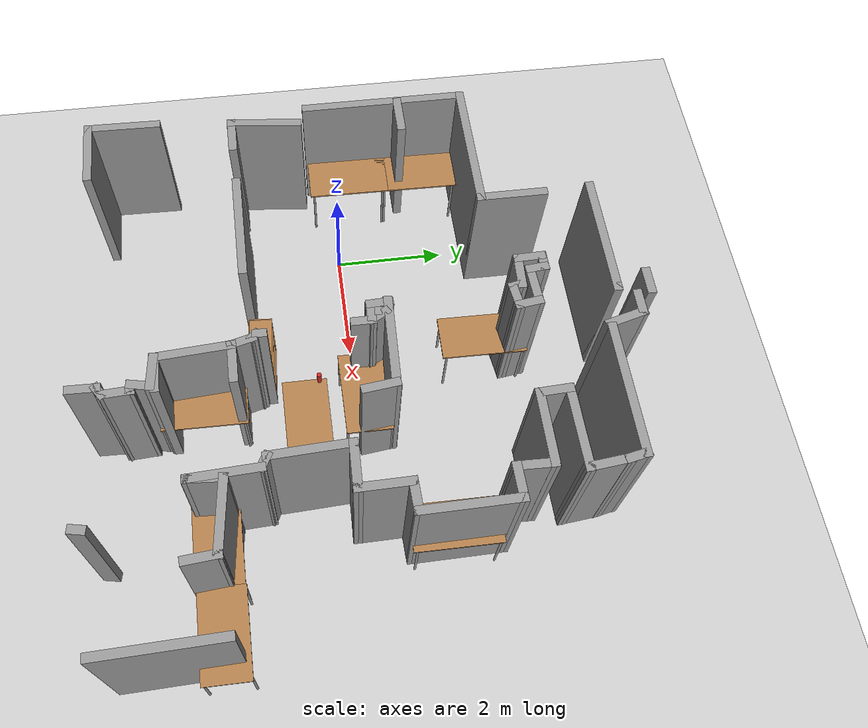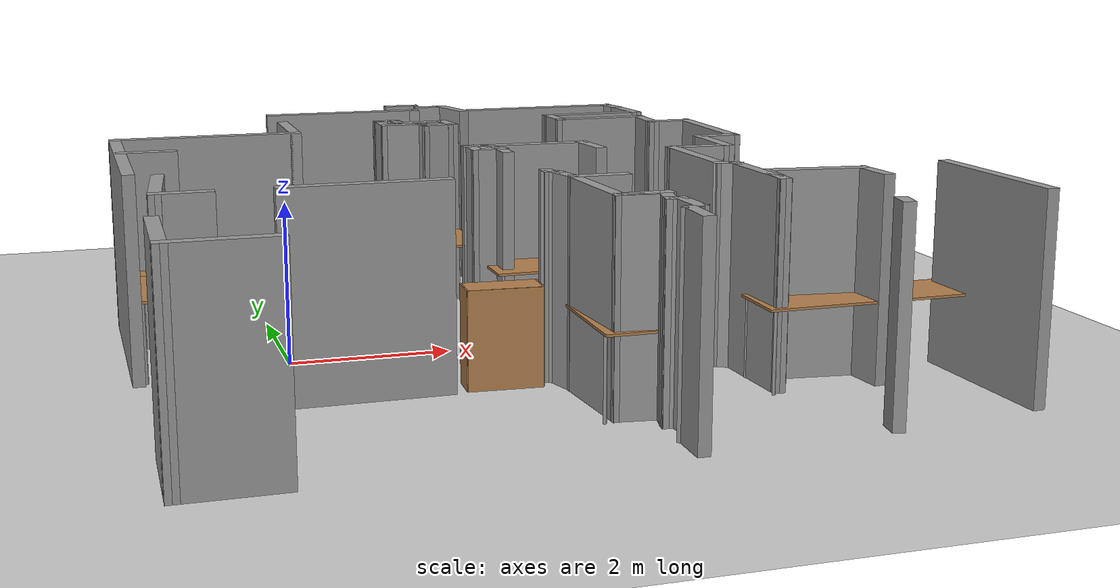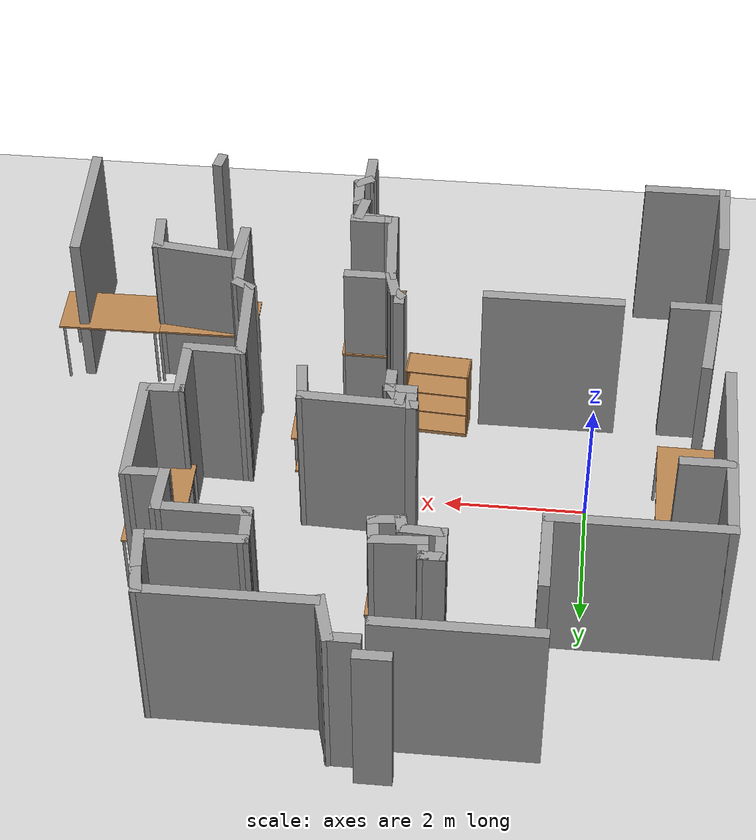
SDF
<sdf version="1.6">
 <world name="default">
  <light name="sun" type="directional">
   <pose>0 0 10 0 -0 0</pose>
   <diffuse>0.8 0.8 0.8 1</diffuse>
   <specular>0.2 0.2 0.2 1</specular>
   <attenuation>
    <range>1000</range>
    <constant>0.9</constant>
    <linear>0.01</linear>
    <quadratic>0.001</quadratic>
   </attenuation>
   <direction>-0.5 0.1 -0.9</direction>
  </light>
  <model name="ground_plane">
   <static>1</static>
   <link name="link">
    <collision name="collision">
     <geometry><plane><normal>0 0 1</normal><size>100 100</size></plane></geometry>
     <surface><friction><ode><mu>100</mu><mu2>50</mu2></ode></friction></surface>
    </collision>
    <visual name="visual">
     <cast_shadows>0</cast_shadows>
     <geometry><plane><normal>0 0 1</normal><size>100 100</size></plane></geometry>
     <material>
      <script><uri>file://media/materials/scripts/gazebo.material</uri><name>Gazebo/Grey</name></script>
     </material>
    </visual>
   </link>
  </model>
  <gravity>0 0 -9.8</gravity>
  <magnetic_field>6e-06 2.3e-05 -4.2e-05</magnetic_field>
  <atmosphere type="adiabatic"/>
  <physics name="default_physics" default="0" type="ode">
   <max_step_size>0.001</max_step_size>
   <real_time_factor>1</real_time_factor>
   <real_time_update_rate>1000</real_time_update_rate>
  </physics>
  <scene><ambient>0.4 0.4 0.4 1</ambient><background>0.7 0.7 0.7 1</background><shadows>1</shadows></scene>
  <spherical_coordinates>
   <surface_model>EARTH_WGS84</surface_model>
   <latitude_deg>0</latitude_deg>
   <longitude_deg>0</longitude_deg>
   <elevation>0</elevation>
   <heading_deg>0</heading_deg>
  </spherical_coordinates>
  <model name="amtc_draft">
   <pose>2.91854 0.17297 0 0 -0 0</pose>
   <link name="Wall_0">
    <collision name="Wall_0_Collision">
     <geometry><box><size>2.25 0.15 2.5</size></box></geometry>
     <pose>0 0 1.25 0 -0 0</pose>
    </collision>
    <visual name="Wall_0_Visual">
     <pose>0 0 1.25 0 -0 0</pose>
     <geometry><box><size>2.25 0.15 2.5</size></box></geometry>
     <material>
      <script><uri>file://media/materials/scripts/gazebo.material</uri><name>Gazebo/Grey</name></script>
      <ambient>1 1 1 1</ambient>
     </material>
     <meta><layer>0</layer></meta>
    </visual>
    <pose>-1.37369 4.2257 0 0 -0 0</pose>
   </link>
   <link name="Wall_1">
    <collision name="Wall_1_Collision">
     <geometry><box><size>0.15 0.15 2.5</size></box></geometry>
     <pose>0 0 1.25 0 -0 0</pose>
    </collision>
    <visual name="Wall_1_Visual">
     <pose>0 0 1.25 0 -0 0</pose>
     <geometry><box><size>0.15 0.15 2.5</size></box></geometry>
     <material>
      <script><uri>file://media/materials/scripts/gazebo.material</uri><name>Gazebo/Grey</name></script>
      <ambient>1 1 1 1</ambient>
     </material>
     <meta><layer>0</layer></meta>
    </visual>
    <pose>-0.323685 4.2257 0 0 -0 0</pose>
   </link>
   <link name="Wall_11">
    <collision name="Wall_11_Collision">
     <geometry><box><size>2.5 0.15 2.5</size></box></geometry>
     <pose>0 0 1.25 0 -0 0</pose>
    </collision>
    <visual name="Wall_11_Visual">
     <pose>0 0 1.25 0 -0 0</pose>
     <geometry><box><size>2.5 0.15 2.5</size></box></geometry>
     <material>
      <script><uri>file://media/materials/scripts/gazebo.material</uri><name>Gazebo/Grey</name></script>
      <ambient>1 1 1 1</ambient>
     </material>
     <meta><layer>0</layer></meta>
    </visual>
    <pose>-3.56442 2.29394 0 0 -0 0</pose>
   </link>
   <link name="Wall_12">
    <collision name="Wall_12_Collision">
     <geometry><box><size>1.25 0.15 2.5</size></box></geometry>
     <pose>0 0 1.25 0 -0 0</pose>
    </collision>
    <visual name="Wall_12_Visual">
     <pose>0 0 1.25 0 -0 0</pose>
     <geometry><box><size>1.25 0.15 2.5</size></box></geometry>
     <material>
      <script><uri>file://media/materials/scripts/gazebo.material</uri><name>Gazebo/Grey</name></script>
      <ambient>1 1 1 1</ambient>
     </material>
     <meta><layer>0</layer></meta>
    </visual>
    <pose>-2.38942 2.84394 0 0 -0 1.5708</pose>
   </link>
   <link name="Wall_14">
    <collision name="Wall_14_Collision">
     <geometry><box><size>3 0.15 2.5</size></box></geometry>
     <pose>0 0 1.25 0 -0 0</pose>
    </collision>
    <visual name="Wall_14_Visual">
     <pose>0 0 1.25 0 -0 0</pose>
     <geometry><box><size>3 0.15 2.5</size></box></geometry>
     <material>
      <script><uri>file://media/materials/scripts/gazebo.material</uri><name>Gazebo/Grey</name></script>
      <ambient>1 1 1 1</ambient>
     </material>
     <meta><layer>0</layer></meta>
    </visual>
    <pose>-4.73942 0.868941 0 0 0 -1.5708</pose>
   </link>
   <link name="Wall_16">
    <collision name="Wall_16_Collision">
     <geometry><box><size>1.34561 0.15 2.5</size></box></geometry>
     <pose>0 0 1.25 0 -0 0</pose>
    </collision>
    <visual name="Wall_16_Visual">
     <pose>0 0 1.25 0 -0 0</pose>
     <geometry><box><size>1.34561 0.15 2.5</size></box></geometry>
     <material>
      <script><uri>file://media/materials/scripts/gazebo.material</uri><name>Gazebo/Grey</name></script>
      <ambient>1 1 1 1</ambient>
     </material>
     <meta><layer>0</layer></meta>
    </visual>
    <pose>-4.48581 -1.34399 0 0 0 -1.67338</pose>
   </link>
   <link name="Wall_17">
    <collision name="Wall_17_Collision">
     <geometry><box><size>0.709682 0.15 2.5</size></box></geometry>
     <pose>0 0 1.25 0 -0 0</pose>
    </collision>
    <visual name="Wall_17_Visual">
     <pose>0 0 1.25 0 -0 0</pose>
     <geometry><box><size>0.709682 0.15 2.5</size></box></geometry>
     <material>
      <script><uri>file://media/materials/scripts/gazebo.material</uri><name>Gazebo/Grey</name></script>
      <ambient>1 1 1 1</ambient>
     </material>
     <meta><layer>0</layer></meta>
    </visual>
    <pose>-4.26719 -1.93865 0 0 -0 0</pose>
   </link>
   <link name="Wall_19">
    <collision name="Wall_19_Collision">
     <geometry><box><size>2 0.15 2.5</size></box></geometry>
     <pose>0 0 1.25 0 -0 0</pose>
    </collision>
    <visual name="Wall_19_Visual">
     <pose>0 0 1.25 0 -0 0</pose>
     <geometry><box><size>2 0.15 2.5</size></box></geometry>
     <material>
      <script><uri>file://media/materials/scripts/gazebo.material</uri><name>Gazebo/Grey</name></script>
      <ambient>1 1 1 1</ambient>
     </material>
     <meta><layer>0</layer></meta>
    </visual>
    <pose>-2.27529 -1.92116 0 0 -0 0</pose>
   </link>
   <link name="Wall_2">
    <collision name="Wall_2_Collision">
     <geometry><box><size>0.15 0.15 2.5</size></box></geometry>
     <pose>0 0 1.25 0 -0 0</pose>
    </collision>
    <visual name="Wall_2_Visual">
     <pose>0 0 1.25 0 -0 0</pose>
     <geometry><box><size>0.15 0.15 2.5</size></box></geometry>
     <material>
      <script><uri>file://media/materials/scripts/gazebo.material</uri><name>Gazebo/Grey</name></script>
      <ambient>1 1 1 1</ambient>
     </material>
     <meta><layer>0</layer></meta>
    </visual>
    <pose>-0.323685 4.2257 0 0 -0 0</pose>
   </link>
   <link name="Wall_22">
    <collision name="Wall_22_Collision">
     <geometry><box><size>0.25 0.15 2.5</size></box></geometry>
     <pose>0 0 1.25 0 -0 0</pose>
    </collision>
    <visual name="Wall_22_Visual">
     <pose>0 0 1.25 0 -0 0</pose>
     <geometry><box><size>0.25 0.15 2.5</size></box></geometry>
     <material>
      <script><uri>file://media/materials/scripts/gazebo.material</uri><name>Gazebo/Grey</name></script>
      <ambient>1 1 1 1</ambient>
     </material>
     <meta><layer>0</layer></meta>
    </visual>
    <pose>-0.104552 -1.7263 0 0 0 -1.5708</pose>
   </link>
   <link name="Wall_23">
    <collision name="Wall_23_Collision">
     <geometry><box><size>0.25 0.15 2.5</size></box></geometry>
     <pose>0 0 1.25 0 -0 0</pose>
    </collision>
    <visual name="Wall_23_Visual">
     <pose>0 0 1.25 0 -0 0</pose>
     <geometry><box><size>0.25 0.15 2.5</size></box></geometry>
     <material>
      <script><uri>file://media/materials/scripts/gazebo.material</uri><name>Gazebo/Grey</name></script>
      <ambient>1 1 1 1</ambient>
     </material>
     <meta><layer>0</layer></meta>
    </visual>
    <pose>-0.069196 -1.81166 0 0 0 -0.785398</pose>
   </link>
   <link name="Wall_24">
    <collision name="Wall_24_Collision">
     <geometry><box><size>0.5 0.15 2.5</size></box></geometry>
     <pose>0 0 1.25 0 -0 0</pose>
    </collision>
    <visual name="Wall_24_Visual">
     <pose>0 0 1.25 0 -0 0</pose>
     <geometry><box><size>0.5 0.15 2.5</size></box></geometry>
     <material>
      <script><uri>file://media/materials/scripts/gazebo.material</uri><name>Gazebo/Grey</name></script>
      <ambient>1 1 1 1</ambient>
     </material>
     <meta><layer>0</layer></meta>
    </visual>
    <pose>0.011452 -2.01605 0 0 0 -1.309</pose>
   </link>
   <link name="Wall_25">
    <collision name="Wall_25_Collision">
     <geometry><box><size>0.75 0.15 2.5</size></box></geometry>
     <pose>0 0 1.25 0 -0 0</pose>
    </collision>
    <visual name="Wall_25_Visual">
     <pose>0 0 1.25 0 -0 0</pose>
     <geometry><box><size>0.75 0.15 2.5</size></box></geometry>
     <material>
      <script><uri>file://media/materials/scripts/gazebo.material</uri><name>Gazebo/Grey</name></script>
      <ambient>1 1 1 1</ambient>
     </material>
     <meta><layer>0</layer></meta>
    </visual>
    <pose>0.356746 -2.18509 0 0 -0 0</pose>
   </link>
   <link name="Wall_29">
    <collision name="Wall_29_Collision">
     <geometry><box><size>0.5 0.15 2.5</size></box></geometry>
     <pose>0 0 1.25 0 -0 0</pose>
    </collision>
    <visual name="Wall_29_Visual">
     <pose>0 0 1.25 0 -0 0</pose>
     <geometry><box><size>0.5 0.15 2.5</size></box></geometry>
     <material>
      <script><uri>file://media/materials/scripts/gazebo.material</uri><name>Gazebo/Grey</name></script>
      <ambient>1 1 1 1</ambient>
     </material>
     <meta><layer>0</layer></meta>
    </visual>
    <pose>0.518345 -3.42555 0 0 -0 3.14159</pose>
   </link>
   <link name="Wall_30">
    <collision name="Wall_30_Collision">
     <geometry><box><size>0.25 0.15 2.5</size></box></geometry>
     <pose>0 0 1.25 0 -0 0</pose>
    </collision>
    <visual name="Wall_30_Visual">
     <pose>0 0 1.25 0 -0 0</pose>
     <geometry><box><size>0.25 0.15 2.5</size></box></geometry>
     <material>
      <script><uri>file://media/materials/scripts/gazebo.material</uri><name>Gazebo/Grey</name></script>
      <ambient>1 1 1 1</ambient>
     </material>
     <meta><layer>0</layer></meta>
    </visual>
    <pose>0.293345 -3.42555 0 0 -0 3.14159</pose>
   </link>
   <link name="Wall_32">
    <collision name="Wall_32_Collision">
     <geometry><box><size>1.40231 0.15 2.5</size></box></geometry>
     <pose>0 0 1.25 0 -0 0</pose>
    </collision>
    <visual name="Wall_32_Visual">
     <pose>0 0 1.25 0 -0 0</pose>
     <geometry><box><size>1.40231 0.15 2.5</size></box></geometry>
     <material>
      <script><uri>file://media/materials/scripts/gazebo.material</uri><name>Gazebo/Grey</name></script>
      <ambient>1 1 1 1</ambient>
     </material>
     <meta><layer>0</layer></meta>
    </visual>
    <pose>0.101132 -2.80967 0 0 0 -1.49985</pose>
   </link>
   <link name="Wall_33">
    <collision name="Wall_33_Collision">
     <geometry><box><size>0.658008 0.15 2.5</size></box></geometry>
     <pose>0 0 1.25 0 -0 0</pose>
    </collision>
    <visual name="Wall_33_Visual">
     <pose>0 0 1.25 0 -0 0</pose>
     <geometry><box><size>0.658008 0.15 2.5</size></box></geometry>
     <material>
      <script><uri>file://media/materials/scripts/gazebo.material</uri><name>Gazebo/Grey</name></script>
      <ambient>1 1 1 1</ambient>
     </material>
     <meta><layer>0</layer></meta>
    </visual>
    <pose>0.397693 -3.46468 0 0 0 -0.120109</pose>
   </link>
   <link name="Wall_34">
    <collision name="Wall_34_Collision">
     <geometry><box><size>0.460375 0.15 2.5</size></box></geometry>
     <pose>0 0 1.25 0 -0 0</pose>
    </collision>
    <visual name="Wall_34_Visual">
     <pose>0 0 1.25 0 -0 0</pose>
     <geometry><box><size>0.460375 0.15 2.5</size></box></geometry>
     <material>
      <script><uri>file://media/materials/scripts/gazebo.material</uri><name>Gazebo/Grey</name></script>
      <ambient>1 1 1 1</ambient>
     </material>
     <meta><layer>0</layer></meta>
    </visual>
    <pose>0.619432 -3.64729 0 0 0 -1.76819</pose>
   </link>
   <link name="Wall_35">
    <collision name="Wall_35_Collision">
     <geometry><box><size>0.25471 0.15 2.5</size></box></geometry>
     <pose>0 0 1.25 0 -0 0</pose>
    </collision>
    <visual name="Wall_35_Visual">
     <pose>0 0 1.25 0 -0 0</pose>
     <geometry><box><size>0.25471 0.15 2.5</size></box></geometry>
     <material>
      <script><uri>file://media/materials/scripts/gazebo.material</uri><name>Gazebo/Grey</name></script>
      <ambient>1 1 1 1</ambient>
     </material>
     <meta><layer>0</layer></meta>
    </visual>
    <pose>0.641171 -3.80381 0 0 0 -0.083141</pose>
   </link>
   <link name="Wall_36">
    <collision name="Wall_36_Collision">
     <geometry><box><size>0.594245 0.15 2.5</size></box></geometry>
     <pose>0 0 1.25 0 -0 0</pose>
    </collision>
    <visual name="Wall_36_Visual">
     <pose>0 0 1.25 0 -0 0</pose>
     <geometry><box><size>0.594245 0.15 2.5</size></box></geometry>
     <material>
      <script><uri>file://media/materials/scripts/gazebo.material</uri><name>Gazebo/Grey</name></script>
      <ambient>1 1 1 1</ambient>
     </material>
     <meta><layer>0</layer></meta>
    </visual>
    <pose>0.706388 -4.0299 0 0 0 -1.51204</pose>
   </link>
   <link name="Wall_37">
    <collision name="Wall_37_Collision">
     <geometry><box><size>0.306763 0.15 2.5</size></box></geometry>
     <pose>0 0 1.25 0 -0 0</pose>
    </collision>
    <visual name="Wall_37_Visual">
     <pose>0 0 1.25 0 -0 0</pose>
     <geometry><box><size>0.306763 0.15 2.5</size></box></geometry>
     <material>
      <script><uri>file://media/materials/scripts/gazebo.material</uri><name>Gazebo/Grey</name></script>
      <ambient>1 1 1 1</ambient>
     </material>
     <meta><layer>0</layer></meta>
    </visual>
    <pose>0.654214 -4.29512 0 0 0 -2.55359</pose>
   </link>
   <link name="Wall_38">
    <collision name="Wall_38_Collision">
     <geometry><box><size>0.576176 0.15 2.5</size></box></geometry>
     <pose>0 0 1.25 0 -0 0</pose>
    </collision>
    <visual name="Wall_38_Visual">
     <pose>0 0 1.25 0 -0 0</pose>
     <geometry><box><size>0.576176 0.15 2.5</size></box></geometry>
     <material>
      <script><uri>file://media/materials/scripts/gazebo.material</uri><name>Gazebo/Grey</name></script>
      <ambient>1 1 1 1</ambient>
     </material>
     <meta><layer>0</layer></meta>
    </visual>
    <pose>0.584649 -4.55164 0 0 0 -1.5912</pose>
   </link>
   <link name="Wall_4">
    <collision name="Wall_4_Collision">
     <geometry><box><size>0.5 0.15 2.5</size></box></geometry>
     <pose>0 0 1.25 0 -0 0</pose>
    </collision>
    <visual name="Wall_4_Visual">
     <pose>0 0 1.25 0 -0 0</pose>
     <geometry><box><size>0.5 0.15 2.5</size></box></geometry>
     <material>
      <script><uri>file://media/materials/scripts/gazebo.material</uri><name>Gazebo/Grey</name></script>
      <ambient>1 1 1 1</ambient>
     </material>
     <meta><layer>0</layer></meta>
    </visual>
    <pose>-0.385685 4.7662 0 0 -0 0</pose>
   </link>
   <link name="Wall_40">
    <collision name="Wall_40_Collision">
     <geometry><box><size>0.291555 0.15 2.5</size></box></geometry>
     <pose>0 0 1.25 0 -0 0</pose>
    </collision>
    <visual name="Wall_40_Visual">
     <pose>0 0 1.25 0 -0 0</pose>
     <geometry><box><size>0.291555 0.15 2.5</size></box></geometry>
     <material>
      <script><uri>file://media/materials/scripts/gazebo.material</uri><name>Gazebo/Grey</name></script>
      <ambient>1 1 1 1</ambient>
     </material>
     <meta><layer>0</layer></meta>
    </visual>
    <pose>2.8803 -4.59947 0 0 -0 1.38545</pose>
   </link>
   <link name="Wall_42">
    <collision name="Wall_42_Collision">
     <geometry><box><size>2.12514 0.15 2.5</size></box></geometry>
     <pose>0 0 1.25 0 -0 0</pose>
    </collision>
    <visual name="Wall_42_Visual">
     <pose>0 0 1.25 0 -0 0</pose>
     <geometry><box><size>2.12514 0.15 2.5</size></box></geometry>
     <material>
      <script><uri>file://media/materials/scripts/gazebo.material</uri><name>Gazebo/Grey</name></script>
      <ambient>1 1 1 1</ambient>
     </material>
     <meta><layer>0</layer></meta>
    </visual>
    <pose>4.70204 -3.4386 0 0 -0 1.60602</pose>
   </link>
   <link name="Wall_44">
    <collision name="Wall_44_Collision">
     <geometry><box><size>0.638894 0.15 2.5</size></box></geometry>
     <pose>0 0 1.25 0 -0 0</pose>
    </collision>
    <visual name="Wall_44_Visual">
     <pose>0 0 1.25 0 -0 0</pose>
     <geometry><box><size>0.638894 0.15 2.5</size></box></geometry>
     <material>
      <script><uri>file://media/materials/scripts/gazebo.material</uri><name>Gazebo/Grey</name></script>
      <ambient>1 1 1 1</ambient>
     </material>
     <meta><layer>0</layer></meta>
    </visual>
    <pose>3.49769 -2.80816 0 0 -0 1.65985</pose>
   </link>
   <link name="Wall_45">
    <collision name="Wall_45_Collision">
     <geometry><box><size>1.33213 0.15 2.5</size></box></geometry>
     <pose>0 0 1.25 0 -0 0</pose>
    </collision>
    <visual name="Wall_45_Visual">
     <pose>0 0 1.25 0 -0 0</pose>
     <geometry><box><size>1.33213 0.15 2.5</size></box></geometry>
     <material>
      <script><uri>file://media/materials/scripts/gazebo.material</uri><name>Gazebo/Grey</name></script>
      <ambient>1 1 1 1</ambient>
     </material>
     <meta><layer>0</layer></meta>
    </visual>
    <pose>2.889 -2.49512 0 0 -0 3.02362</pose>
   </link>
   <link name="Wall_46">
    <collision name="Wall_46_Collision">
     <geometry><box><size>0.707608 0.15 2.5</size></box></geometry>
     <pose>0 0 1.25 0 -0 0</pose>
    </collision>
    <visual name="Wall_46_Visual">
     <pose>0 0 1.25 0 -0 0</pose>
     <geometry><box><size>0.707608 0.15 2.5</size></box></geometry>
     <material>
      <script><uri>file://media/materials/scripts/gazebo.material</uri><name>Gazebo/Grey</name></script>
      <ambient>1 1 1 1</ambient>
     </material>
     <meta><layer>0</layer></meta>
    </visual>
    <pose>2.28465 -2.70382 0 0 0 -1.63322</pose>
   </link>
   <link name="Wall_47">
    <collision name="Wall_47_Collision">
     <geometry><box><size>1.28207 0.15 2.5</size></box></geometry>
     <pose>0 0 1.25 0 -0 0</pose>
    </collision>
    <visual name="Wall_47_Visual">
     <pose>0 0 1.25 0 -0 0</pose>
     <geometry><box><size>1.28207 0.15 2.5</size></box></geometry>
     <material>
      <script><uri>file://media/materials/scripts/gazebo.material</uri><name>Gazebo/Grey</name></script>
      <ambient>1 1 1 1</ambient>
     </material>
     <meta><layer>0</layer></meta>
    </visual>
    <pose>2.23682 -2.41686 0 0 -0 1.62459</pose>
   </link>
   <link name="Wall_48">
    <collision name="Wall_48_Collision">
     <geometry><box><size>0.348482 0.15 2.5</size></box></geometry>
     <pose>0 0 1.25 0 -0 0</pose>
    </collision>
    <visual name="Wall_48_Visual">
     <pose>0 0 1.25 0 -0 0</pose>
     <geometry><box><size>0.348482 0.15 2.5</size></box></geometry>
     <material>
      <script><uri>file://media/materials/scripts/gazebo.material</uri><name>Gazebo/Grey</name></script>
      <ambient>1 1 1 1</ambient>
     </material>
     <meta><layer>0</layer></meta>
    </visual>
    <pose>2.11943 -1.80381 0 0 -0 2.63875</pose>
   </link>
   <link name="Wall_49">
    <collision name="Wall_49_Collision">
     <geometry><box><size>1.48273 0.15 2.5</size></box></geometry>
     <pose>0 0 1.25 0 -0 0</pose>
    </collision>
    <visual name="Wall_49_Visual">
     <pose>0 0 1.25 0 -0 0</pose>
     <geometry><box><size>1.48273 0.15 2.5</size></box></geometry>
     <material>
      <script><uri>file://media/materials/scripts/gazebo.material</uri><name>Gazebo/Grey</name></script>
      <ambient>1 1 1 1</ambient>
     </material>
     <meta><layer>0</layer></meta>
    </visual>
    <pose>1.99769 -1.09077 0 0 -0 1.62304</pose>
   </link>
   <link name="Wall_50">
    <collision name="Wall_50_Collision">
     <geometry><box><size>0.883246 0.15 2.5</size></box></geometry>
     <pose>0 0 1.25 0 -0 0</pose>
    </collision>
    <visual name="Wall_50_Visual">
     <pose>0 0 1.25 0 -0 0</pose>
     <geometry><box><size>0.883246 0.15 2.5</size></box></geometry>
     <material>
      <script><uri>file://media/materials/scripts/gazebo.material</uri><name>Gazebo/Grey</name></script>
      <ambient>1 1 1 1</ambient>
     </material>
     <meta><layer>0</layer></meta>
    </visual>
    <pose>2.32948 -0.434793 0 0 0 -0.0252</pose>
   </link>
   <link name="Wall_51">
    <collision name="Wall_51_Collision">
     <geometry><box><size>0.986619 0.15 2.5</size></box></geometry>
     <pose>0 0 1.25 0 -0 0</pose>
    </collision>
    <visual name="Wall_51_Visual">
     <pose>0 0 1.25 0 -0 0</pose>
     <geometry><box><size>0.986619 0.15 2.5</size></box></geometry>
     <material>
      <script><uri>file://media/materials/scripts/gazebo.material</uri><name>Gazebo/Grey</name></script>
      <ambient>1 1 1 1</ambient>
     </material>
     <meta><layer>0</layer></meta>
    </visual>
    <pose>2.68845 -0.025792 0 0 -0 1.58898</pose>
   </link>
   <link name="Wall_52">
    <collision name="Wall_52_Collision">
     <geometry><box><size>0.621716 0.15 2.5</size></box></geometry>
     <pose>0 0 1.25 0 -0 0</pose>
    </collision>
    <visual name="Wall_52_Visual">
     <pose>0 0 1.25 0 -0 0</pose>
     <geometry><box><size>0.621716 0.15 2.5</size></box></geometry>
     <material>
      <script><uri>file://media/materials/scripts/gazebo.material</uri><name>Gazebo/Grey</name></script>
      <ambient>1 1 1 1</ambient>
     </material>
     <meta><layer>0</layer></meta>
    </visual>
    <pose>2.91659 0.400053 0 0 -0 0.032247</pose>
   </link>
   <link name="Wall_53">
    <collision name="Wall_53_Collision">
     <geometry><box><size>1.72966 0.15 2.5</size></box></geometry>
     <pose>0 0 1.25 0 -0 0</pose>
    </collision>
    <visual name="Wall_53_Visual">
     <pose>0 0 1.25 0 -0 0</pose>
     <geometry><box><size>1.72966 0.15 2.5</size></box></geometry>
     <material>
      <script><uri>file://media/materials/scripts/gazebo.material</uri><name>Gazebo/Grey</name></script>
      <ambient>1 1 1 1</ambient>
     </material>
     <meta><layer>0</layer></meta>
    </visual>
    <pose>3.13851 1.19737 0 0 -0 1.58828</pose>
   </link>
   <link name="Wall_54">
    <collision name="Wall_54_Collision">
     <geometry><box><size>0.656131 0.15 2.5</size></box></geometry>
     <pose>0 0 1.25 0 -0 0</pose>
    </collision>
    <visual name="Wall_54_Visual">
     <pose>0 0 1.25 0 -0 0</pose>
     <geometry><box><size>0.656131 0.15 2.5</size></box></geometry>
     <material>
      <script><uri>file://media/materials/scripts/gazebo.material</uri><name>Gazebo/Grey</name></script>
      <ambient>1 1 1 1</ambient>
     </material>
     <meta><layer>0</layer></meta>
    </visual>
    <pose>2.87171 1.98133 0 0 0 -3.11887</pose>
   </link>
   <link name="Wall_55">
    <collision name="Wall_55_Collision">
     <geometry><box><size>0.736613 0.15 2.5</size></box></geometry>
     <pose>0 0 1.25 0 -0 0</pose>
    </collision>
    <visual name="Wall_55_Visual">
     <pose>0 0 1.25 0 -0 0</pose>
     <geometry><box><size>0.736613 0.15 2.5</size></box></geometry>
     <material>
      <script><uri>file://media/materials/scripts/gazebo.material</uri><name>Gazebo/Grey</name></script>
      <ambient>1 1 1 1</ambient>
     </material>
     <meta><layer>0</layer></meta>
    </visual>
    <pose>2.62446 2.26883 0 0 -0 1.55119</pose>
   </link>
   <link name="Wall_56">
    <collision name="Wall_56_Collision">
     <geometry><box><size>1.33472 0.15 2.5</size></box></geometry>
     <pose>0 0 1.25 0 -0 0</pose>
    </collision>
    <visual name="Wall_56_Visual">
     <pose>0 0 1.25 0 -0 0</pose>
     <geometry><box><size>1.33472 0.15 2.5</size></box></geometry>
     <material>
      <script><uri>file://media/materials/scripts/gazebo.material</uri><name>Gazebo/Grey</name></script>
      <ambient>1 1 1 1</ambient>
     </material>
     <meta><layer>0</layer></meta>
    </visual>
    <pose>2.03796 2.56208 0 0 -0 3.14159</pose>
   </link>
   <link name="Wall_57">
    <collision name="Wall_57_Collision">
     <geometry><box><size>0.633547 0.15 2.5</size></box></geometry>
     <pose>0 0 1.25 0 -0 0</pose>
    </collision>
    <visual name="Wall_57_Visual">
     <pose>0 0 1.25 0 -0 0</pose>
     <geometry><box><size>0.633547 0.15 2.5</size></box></geometry>
     <material>
      <script><uri>file://media/materials/scripts/gazebo.material</uri><name>Gazebo/Grey</name></script>
      <ambient>1 1 1 1</ambient>
     </material>
     <meta><layer>0</layer></meta>
    </visual>
    <pose>1.43421 2.80357 0 0 -0 1.61838</pose>
   </link>
   <link name="Wall_58">
    <collision name="Wall_58_Collision">
     <geometry><box><size>1.4842 0.15 2.5</size></box></geometry>
     <pose>0 0 1.25 0 -0 0</pose>
    </collision>
    <visual name="Wall_58_Visual">
     <pose>0 0 1.25 0 -0 0</pose>
     <geometry><box><size>1.4842 0.15 2.5</size></box></geometry>
     <material>
      <script><uri>file://media/materials/scripts/gazebo.material</uri><name>Gazebo/Grey</name></script>
      <ambient>1 1 1 1</ambient>
     </material>
     <meta><layer>0</layer></meta>
    </visual>
    <pose>2.08971 3.05658 0 0 -0 0.01724</pose>
   </link>
   <link name="Wall_59">
    <collision name="Wall_59_Collision">
     <geometry><box><size>0.786253 0.15 2.5</size></box></geometry>
     <pose>0 0 1.25 0 -0 0</pose>
    </collision>
    <visual name="Wall_59_Visual">
     <pose>0 0 1.25 0 -0 0</pose>
     <geometry><box><size>0.786253 0.15 2.5</size></box></geometry>
     <material>
      <script><uri>file://media/materials/scripts/gazebo.material</uri><name>Gazebo/Grey</name></script>
      <ambient>1 1 1 1</ambient>
     </material>
     <meta><layer>0</layer></meta>
    </visual>
    <pose>2.72221 3.38433 0 0 -0 1.67946</pose>
   </link>
   <link name="Wall_60">
    <collision name="Wall_60_Collision">
     <geometry><box><size>0.431926 0.15 2.5</size></box></geometry>
     <pose>0 0 1.25 0 -0 0</pose>
    </collision>
    <visual name="Wall_60_Visual">
     <pose>0 0 1.25 0 -0 0</pose>
     <geometry><box><size>0.431926 0.15 2.5</size></box></geometry>
     <material>
      <script><uri>file://media/materials/scripts/gazebo.material</uri><name>Gazebo/Grey</name></script>
      <ambient>1 1 1 1</ambient>
     </material>
     <meta><layer>0</layer></meta>
    </visual>
    <pose>2.65896 3.83858 0 0 -0 1.77619</pose>
   </link>
   <link name="Wall_61">
    <collision name="Wall_61_Collision">
     <geometry><box><size>2.36953 0.15 2.5</size></box></geometry>
     <pose>0 0 1.25 0 -0 0</pose>
    </collision>
    <visual name="Wall_61_Visual">
     <pose>0 0 1.25 0 -0 0</pose>
     <geometry><box><size>2.36953 0.15 2.5</size></box></geometry>
     <material>
      <script><uri>file://media/materials/scripts/gazebo.material</uri><name>Gazebo/Grey</name></script>
      <ambient>1 1 1 1</ambient>
     </material>
     <meta><layer>0</layer></meta>
    </visual>
    <pose>1.52046 3.97083 0 0 0 -3.13641</pose>
   </link>
   <link name="Wall_63">
    <collision name="Wall_63_Collision">
     <geometry><box><size>0.552664 0.15 2.5</size></box></geometry>
     <pose>0 0 1.25 0 -0 0</pose>
    </collision>
    <visual name="Wall_63_Visual">
     <pose>0 0 1.25 0 -0 0</pose>
     <geometry><box><size>0.552664 0.15 2.5</size></box></geometry>
     <material>
      <script><uri>file://media/materials/scripts/gazebo.material</uri><name>Gazebo/Grey</name></script>
      <ambient>1 1 1 1</ambient>
     </material>
     <meta><layer>0</layer></meta>
    </visual>
    <pose>-1.06704 2.88983 0 0 0 -1.54223</pose>
   </link>
   <link name="Wall_64">
    <collision name="Wall_64_Collision">
     <geometry><box><size>0.656522 0.15 2.5</size></box></geometry>
     <pose>0 0 1.25 0 -0 0</pose>
    </collision>
    <visual name="Wall_64_Visual">
     <pose>0 0 1.25 0 -0 0</pose>
     <geometry><box><size>0.656522 0.15 2.5</size></box></geometry>
     <material>
      <script><uri>file://media/materials/scripts/gazebo.material</uri><name>Gazebo/Grey</name></script>
      <ambient>1 1 1 1</ambient>
     </material>
     <meta><layer>0</layer></meta>
    </visual>
    <pose>-0.808293 2.67707 0 0 0 -0.045423</pose>
   </link>
   <link name="Wall_65">
    <collision name="Wall_65_Collision">
     <geometry><box><size>0.314655 0.15 2.5</size></box></geometry>
     <pose>0 0 1.25 0 -0 0</pose>
    </collision>
    <visual name="Wall_65_Visual">
     <pose>0 0 1.25 0 -0 0</pose>
     <geometry><box><size>0.314655 0.15 2.5</size></box></geometry>
     <material>
      <script><uri>file://media/materials/scripts/gazebo.material</uri><name>Gazebo/Grey</name></script>
      <ambient>1 1 1 1</ambient>
     </material>
     <meta><layer>0</layer></meta>
    </visual>
    <pose>-0.538043 2.58507 0 0 0 -1.3597</pose>
   </link>
   <link name="Wall_66">
    <collision name="Wall_66_Collision">
     <geometry><box><size>0.509455 0.15 2.5</size></box></geometry>
     <pose>0 0 1.25 0 -0 0</pose>
    </collision>
    <visual name="Wall_66_Visual">
     <pose>0 0 1.25 0 -0 0</pose>
     <geometry><box><size>0.509455 0.15 2.5</size></box></geometry>
     <material>
      <script><uri>file://media/materials/scripts/gazebo.material</uri><name>Gazebo/Grey</name></script>
      <ambient>1 1 1 1</ambient>
     </material>
     <meta><layer>0</layer></meta>
    </visual>
    <pose>-0.342543 2.52758 0 0 -0 0.128323</pose>
   </link>
   <link name="Wall_67">
    <collision name="Wall_67_Collision">
     <geometry><box><size>0.486657 0.15 2.5</size></box></geometry>
     <pose>0 0 1.25 0 -0 0</pose>
    </collision>
    <visual name="Wall_67_Visual">
     <pose>0 0 1.25 0 -0 0</pose>
     <geometry><box><size>0.486657 0.15 2.5</size></box></geometry>
     <material>
      <script><uri>file://media/materials/scripts/gazebo.material</uri><name>Gazebo/Grey</name></script>
      <ambient>1 1 1 1</ambient>
     </material>
     <meta><layer>0</layer></meta>
    </visual>
    <pose>-0.187293 2.71733 0 0 -0 1.70786</pose>
   </link>
   <link name="Wall_68">
    <collision name="Wall_68_Collision">
     <geometry><box><size>0.772701 0.15 2.5</size></box></geometry>
     <pose>0 0 1.25 0 -0 0</pose>
    </collision>
    <visual name="Wall_68_Visual">
     <pose>0 0 1.25 0 -0 0</pose>
     <geometry><box><size>0.772701 0.15 2.5</size></box></geometry>
     <material>
      <script><uri>file://media/materials/scripts/gazebo.material</uri><name>Gazebo/Grey</name></script>
      <ambient>1 1 1 1</ambient>
     </material>
     <meta><layer>0</layer></meta>
    </visual>
    <pose>-0.520793 2.86682 0 0 0 -3.08609</pose>
   </link>
   <link name="Wall_69">
    <collision name="Wall_69_Collision">
     <geometry><box><size>0.404043 0.15 2.5</size></box></geometry>
     <pose>0 0 1.25 0 -0 0</pose>
    </collision>
    <visual name="Wall_69_Visual">
     <pose>0 0 1.25 0 -0 0</pose>
     <geometry><box><size>0.404043 0.15 2.5</size></box></geometry>
     <material>
      <script><uri>file://media/materials/scripts/gazebo.material</uri><name>Gazebo/Grey</name></script>
      <ambient>1 1 1 1</ambient>
     </material>
     <meta><layer>0</layer></meta>
    </visual>
    <pose>-0.842793 2.97607 0 0 -0 1.66146</pose>
   </link>
   <link name="Wall_70">
    <collision name="Wall_70_Collision">
     <geometry><box><size>0.3685 0.15 2.5</size></box></geometry>
     <pose>0 0 1.25 0 -0 0</pose>
    </collision>
    <visual name="Wall_70_Visual">
     <pose>0 0 1.25 0 -0 0</pose>
     <geometry><box><size>0.3685 0.15 2.5</size></box></geometry>
     <material>
      <script><uri>file://media/materials/scripts/gazebo.material</uri><name>Gazebo/Grey</name></script>
      <ambient>1 1 1 1</ambient>
     </material>
     <meta><layer>0</layer></meta>
    </visual>
    <pose>-0.963543 3.10257 0 0 -0 3.14159</pose>
   </link>
   <link name="Wall_72">
    <collision name="Wall_72_Collision">
     <geometry><box><size>1.65566 0.15 2.5</size></box></geometry>
     <pose>0 0 1.25 0 -0 0</pose>
    </collision>
    <visual name="Wall_72_Visual">
     <pose>0 0 1.25 0 -0 0</pose>
     <geometry><box><size>1.65566 0.15 2.5</size></box></geometry>
     <material>
      <script><uri>file://media/materials/scripts/gazebo.material</uri><name>Gazebo/Grey</name></script>
      <ambient>1 1 1 1</ambient>
     </material>
     <meta><layer>0</layer></meta>
    </visual>
    <pose>0.264041 0.386656 0 0 0 -0.035161</pose>
   </link>
   <link name="Wall_73">
    <collision name="Wall_73_Collision">
     <geometry><box><size>0.652708 0.15 2.5</size></box></geometry>
     <pose>0 0 1.25 0 -0 0</pose>
    </collision>
    <visual name="Wall_73_Visual">
     <pose>0 0 1.25 0 -0 0</pose>
     <geometry><box><size>0.652708 0.15 2.5</size></box></geometry>
     <material>
      <script><uri>file://media/materials/scripts/gazebo.material</uri><name>Gazebo/Grey</name></script>
      <ambient>1 1 1 1</ambient>
     </material>
     <meta><layer>0</layer></meta>
    </visual>
    <pose>1.04665 0.110664 0 0 0 -1.45017</pose>
   </link>
   <link name="Wall_75">
    <collision name="Wall_75_Collision">
     <geometry><box><size>0.460111 0.15 2.5</size></box></geometry>
     <pose>0 0 1.25 0 -0 0</pose>
    </collision>
    <visual name="Wall_75_Visual">
     <pose>0 0 1.25 0 -0 0</pose>
     <geometry><box><size>0.460111 0.15 2.5</size></box></geometry>
     <material>
      <script><uri>file://media/materials/scripts/gazebo.material</uri><name>Gazebo/Grey</name></script>
      <ambient>1 1 1 1</ambient>
     </material>
     <meta><layer>0</layer></meta>
    </visual>
    <pose>-0.458076 0.273235 0 0 0 -1.52205</pose>
   </link>
   <link name="Wall_76">
    <collision name="Wall_76_Collision">
     <geometry><box><size>0.452552 0.15 2.5</size></box></geometry>
     <pose>0 0 1.25 0 -0 0</pose>
    </collision>
    <visual name="Wall_76_Visual">
     <pose>0 0 1.25 0 -0 0</pose>
     <geometry><box><size>0.452552 0.15 2.5</size></box></geometry>
     <material>
      <script><uri>file://media/materials/scripts/gazebo.material</uri><name>Gazebo/Grey</name></script>
      <ambient>1 1 1 1</ambient>
     </material>
     <meta><layer>0</layer></meta>
    </visual>
    <pose>-0.299286 0.114444 0 0 0 -0.024995</pose>
   </link>
   <link name="Wall_77">
    <collision name="Wall_77_Collision">
     <geometry><box><size>0.430691 0.15 2.5</size></box></geometry>
     <pose>0 0 1.25 0 -0 0</pose>
    </collision>
    <visual name="Wall_77_Visual">
     <pose>0 0 1.25 0 -0 0</pose>
     <geometry><box><size>0.430691 0.15 2.5</size></box></geometry>
     <material>
      <script><uri>file://media/materials/scripts/gazebo.material</uri><name>Gazebo/Grey</name></script>
      <ambient>1 1 1 1</ambient>
     </material>
     <meta><layer>0</layer></meta>
    </visual>
    <pose>-0.148058 -0.029223 0 0 0 -1.5708</pose>
   </link>
   <link name="Wall_79">
    <collision name="Wall_79_Collision">
     <geometry><box><size>1.37516 0.15 2.5</size></box></geometry>
     <pose>0 0 1.25 0 -0 0</pose>
    </collision>
    <visual name="Wall_79_Visual">
     <pose>0 0 1.25 0 -0 0</pose>
     <geometry><box><size>1.37516 0.15 2.5</size></box></geometry>
     <material>
      <script><uri>file://media/materials/scripts/gazebo.material</uri><name>Gazebo/Grey</name></script>
      <ambient>1 1 1 1</ambient>
     </material>
     <meta><layer>0</layer></meta>
    </visual>
    <pose>-4.68522 -3.91186 0 0 0 -1.58931</pose>
   </link>
   <link name="Wall_8">
    <collision name="Wall_8_Collision">
     <geometry><box><size>0.5 0.15 2.5</size></box></geometry>
     <pose>0 0 1.25 0 -0 0</pose>
    </collision>
    <visual name="Wall_8_Visual">
     <pose>0 0 1.25 0 -0 0</pose>
     <geometry><box><size>0.5 0.15 2.5</size></box></geometry>
     <material>
      <script><uri>file://media/materials/scripts/gazebo.material</uri><name>Gazebo/Grey</name></script>
      <ambient>1 1 1 1</ambient>
     </material>
     <meta><layer>0</layer></meta>
    </visual>
    <pose>0.016815 4.5247 0 0 -0 0</pose>
   </link>
   <link name="Wall_81">
    <collision name="Wall_81_Collision">
     <geometry><box><size>1.25 0.15 2.5</size></box></geometry>
     <pose>0 0 1.25 0 -0 0</pose>
    </collision>
    <visual name="Wall_81_Visual">
     <pose>0 0 1.25 0 -0 0</pose>
     <geometry><box><size>1.25 0.15 2.5</size></box></geometry>
     <material>
      <script><uri>file://media/materials/scripts/gazebo.material</uri><name>Gazebo/Grey</name></script>
      <ambient>1 1 1 1</ambient>
     </material>
     <meta><layer>0</layer></meta>
    </visual>
    <pose>-4.14656 -4.52433 0 0 -0 0</pose>
   </link>
   <link name="Wall_83">
    <collision name="Wall_83_Collision">
     <geometry><box><size>0.75 0.15 2.5</size></box></geometry>
     <pose>0 0 1.25 0 -0 0</pose>
    </collision>
    <visual name="Wall_83_Visual">
     <pose>0 0 1.25 0 -0 0</pose>
     <geometry><box><size>0.75 0.15 2.5</size></box></geometry>
     <material>
      <script><uri>file://media/materials/scripts/gazebo.material</uri><name>Gazebo/Grey</name></script>
      <ambient>1 1 1 1</ambient>
     </material>
     <meta><layer>0</layer></meta>
    </visual>
    <pose>-4.4169 1.12215 0 0 -0 0</pose>
   </link>
   <link name="Wall_85">
    <collision name="Wall_85_Collision">
     <geometry><box><size>0.428876 0.15 2.5</size></box></geometry>
     <pose>0 0 1.25 0 -0 0</pose>
    </collision>
    <visual name="Wall_85_Visual">
     <pose>0 0 1.25 0 -0 0</pose>
     <geometry><box><size>0.428876 0.15 2.5</size></box></geometry>
     <material>
      <script><uri>file://media/materials/scripts/gazebo.material</uri><name>Gazebo/Grey</name></script>
      <ambient>1 1 1 1</ambient>
     </material>
     <meta><layer>0</layer></meta>
    </visual>
    <pose>-0.217864 0.23137 0 0 -0 2.09512</pose>
   </link>
   <link name="Wall_86">
    <collision name="Wall_86_Collision">
     <geometry><box><size>0.256021 0.15 2.5</size></box></geometry>
     <pose>0 0 1.25 0 -0 0</pose>
    </collision>
    <visual name="Wall_86_Visual">
     <pose>0 0 1.25 0 -0 0</pose>
     <geometry><box><size>0.256021 0.15 2.5</size></box></geometry>
     <material>
      <script><uri>file://media/materials/scripts/gazebo.material</uri><name>Gazebo/Grey</name></script>
      <ambient>1 1 1 1</ambient>
     </material>
     <meta><layer>0</layer></meta>
    </visual>
    <pose>-0.294246 0.299474 0 0 0 -1.69515</pose>
   </link>
   <link name="Wall_9">
    <collision name="Wall_9_Collision">
     <geometry><box><size>0.75 0.15 2.5</size></box></geometry>
     <pose>0 0 1.25 0 -0 0</pose>
    </collision>
    <visual name="Wall_9_Visual">
     <pose>0 0 1.25 0 -0 0</pose>
     <geometry><box><size>0.75 0.15 2.5</size></box></geometry>
     <material>
      <script><uri>file://media/materials/scripts/gazebo.material</uri><name>Gazebo/Grey</name></script>
      <ambient>1 1 1 1</ambient>
     </material>
     <meta><layer>0</layer></meta>
    </visual>
    <pose>0.269461 4.23492 0 0 0 -1.309</pose>
   </link>
   <static>1</static>
  </model>
  <model name="table">
   <static>1</static>
   <link name="link">
    <collision name="surface">
     <pose>0 0 1 0 -0 0</pose>
     <geometry><box><size>1.5 0.8 0.03</size></box></geometry>
     <surface><friction><ode><mu>0.6</mu><mu2>0.6</mu2></ode></friction></surface>
    </collision>
    <visual name="visual1">
     <pose>0 0 1 0 -0 0</pose>
     <geometry><box><size>1.5 0.8 0.03</size></box></geometry>
     <material>
      <script><uri>file://media/materials/scripts/gazebo.material</uri><name>Gazebo/Wood</name></script>
     </material>
    </visual>
    <collision name="front_left_leg">
     <pose>0.68 0.38 0.5 0 -0 0</pose>
     <geometry><cylinder><radius>0.02</radius><length>1</length></cylinder></geometry>
    </collision>
    <visual name="front_left_leg">
     <pose>0.68 0.38 0.5 0 -0 0</pose>
     <geometry><cylinder><radius>0.02</radius><length>1</length></cylinder></geometry>
     <material>
      <script><uri>file://media/materials/scripts/gazebo.material</uri><name>Gazebo/Grey</name></script>
     </material>
    </visual>
    <collision name="front_right_leg">
     <pose>0.68 -0.38 0.5 0 -0 0</pose>
     <geometry><cylinder><radius>0.02</radius><length>1</length></cylinder></geometry>
    </collision>
    <visual name="front_right_leg">
     <pose>0.68 -0.38 0.5 0 -0 0</pose>
     <geometry><cylinder><radius>0.02</radius><length>1</length></cylinder></geometry>
     <material>
      <script><uri>file://media/materials/scripts/gazebo.material</uri><name>Gazebo/Grey</name></script>
     </material>
    </visual>
    <collision name="back_right_leg">
     <pose>-0.68 -0.38 0.5 0 -0 0</pose>
     <geometry><cylinder><radius>0.02</radius><length>1</length></cylinder></geometry>
    </collision>
    <visual name="back_right_leg">
     <pose>-0.68 -0.38 0.5 0 -0 0</pose>
     <geometry><cylinder><radius>0.02</radius><length>1</length></cylinder></geometry>
     <material>
      <script><uri>file://media/materials/scripts/gazebo.material</uri><name>Gazebo/Grey</name></script>
     </material>
    </visual>
    <collision name="back_left_leg">
     <pose>-0.68 0.38 0.5 0 -0 0</pose>
     <geometry><cylinder><radius>0.02</radius><length>1</length></cylinder></geometry>
    </collision>
    <visual name="back_left_leg">
     <pose>-0.68 0.38 0.5 0 -0 0</pose>
     <geometry><cylinder><radius>0.02</radius><length>1</length></cylinder></geometry>
     <material>
      <script><uri>file://media/materials/scripts/gazebo.material</uri><name>Gazebo/Grey</name></script>
     </material>
    </visual>
   </link>
   <pose>-1.33827 0.322435 0 0 0 -1.58073</pose>
  </model>
  <model name="table_clone">
   <static>1</static>
   <link name="link">
    <collision name="surface">
     <pose>0 0 1 0 -0 0</pose>
     <geometry><box><size>1.5 0.8 0.03</size></box></geometry>
     <surface><friction><ode><mu>0.6</mu><mu2>0.6</mu2></ode></friction></surface>
    </collision>
    <visual name="visual1">
     <pose>0 0 1 0 -0 0</pose>
     <geometry><box><size>1.5 0.8 0.03</size></box></geometry>
     <material>
      <script><uri>file://media/materials/scripts/gazebo.material</uri><name>Gazebo/Wood</name></script>
     </material>
    </visual>
    <collision name="front_left_leg">
     <pose>0.68 0.38 0.5 0 -0 0</pose>
     <geometry><cylinder><radius>0.02</radius><length>1</length></cylinder></geometry>
    </collision>
    <visual name="front_left_leg">
     <pose>0.68 0.38 0.5 0 -0 0</pose>
     <geometry><cylinder><radius>0.02</radius><length>1</length></cylinder></geometry>
     <material>
      <script><uri>file://media/materials/scripts/gazebo.material</uri><name>Gazebo/Grey</name></script>
     </material>
    </visual>
    <collision name="front_right_leg">
     <pose>0.68 -0.38 0.5 0 -0 0</pose>
     <geometry><cylinder><radius>0.02</radius><length>1</length></cylinder></geometry>
    </collision>
    <visual name="front_right_leg">
     <pose>0.68 -0.38 0.5 0 -0 0</pose>
     <geometry><cylinder><radius>0.02</radius><length>1</length></cylinder></geometry>
     <material>
      <script><uri>file://media/materials/scripts/gazebo.material</uri><name>Gazebo/Grey</name></script>
     </material>
    </visual>
    <collision name="back_right_leg">
     <pose>-0.68 -0.38 0.5 0 -0 0</pose>
     <geometry><cylinder><radius>0.02</radius><length>1</length></cylinder></geometry>
    </collision>
    <visual name="back_right_leg">
     <pose>-0.68 -0.38 0.5 0 -0 0</pose>
     <geometry><cylinder><radius>0.02</radius><length>1</length></cylinder></geometry>
     <material>
      <script><uri>file://media/materials/scripts/gazebo.material</uri><name>Gazebo/Grey</name></script>
     </material>
    </visual>
    <collision name="back_left_leg">
     <pose>-0.68 0.38 0.5 0 -0 0</pose>
     <geometry><cylinder><radius>0.02</radius><length>1</length></cylinder></geometry>
    </collision>
    <visual name="back_left_leg">
     <pose>-0.68 0.38 0.5 0 -0 0</pose>
     <geometry><cylinder><radius>0.02</radius><length>1</length></cylinder></geometry>
     <material>
      <script><uri>file://media/materials/scripts/gazebo.material</uri><name>Gazebo/Grey</name></script>
     </material>
    </visual>
   </link>
   <pose>-1.32325 1.64119 0 0 0 -1.58073</pose>
  </model>
  <model name="table_clone_0">
   <static>1</static>
   <link name="link">
    <collision name="surface">
     <pose>0 0 1 0 -0 0</pose>
     <geometry><box><size>1.5 0.8 0.03</size></box></geometry>
     <surface><friction><ode><mu>0.6</mu><mu2>0.6</mu2></ode></friction></surface>
    </collision>
    <visual name="visual1">
     <pose>0 0 1 0 -0 0</pose>
     <geometry><box><size>1.5 0.8 0.03</size></box></geometry>
     <material>
      <script><uri>file://media/materials/scripts/gazebo.material</uri><name>Gazebo/Wood</name></script>
     </material>
    </visual>
    <collision name="front_left_leg">
     <pose>0.68 0.38 0.5 0 -0 0</pose>
     <geometry><cylinder><radius>0.02</radius><length>1</length></cylinder></geometry>
    </collision>
    <visual name="front_left_leg">
     <pose>0.68 0.38 0.5 0 -0 0</pose>
     <geometry><cylinder><radius>0.02</radius><length>1</length></cylinder></geometry>
     <material>
      <script><uri>file://media/materials/scripts/gazebo.material</uri><name>Gazebo/Grey</name></script>
     </material>
    </visual>
    <collision name="front_right_leg">
     <pose>0.68 -0.38 0.5 0 -0 0</pose>
     <geometry><cylinder><radius>0.02</radius><length>1</length></cylinder></geometry>
    </collision>
    <visual name="front_right_leg">
     <pose>0.68 -0.38 0.5 0 -0 0</pose>
     <geometry><cylinder><radius>0.02</radius><length>1</length></cylinder></geometry>
     <material>
      <script><uri>file://media/materials/scripts/gazebo.material</uri><name>Gazebo/Grey</name></script>
     </material>
    </visual>
    <collision name="back_right_leg">
     <pose>-0.68 -0.38 0.5 0 -0 0</pose>
     <geometry><cylinder><radius>0.02</radius><length>1</length></cylinder></geometry>
    </collision>
    <visual name="back_right_leg">
     <pose>-0.68 -0.38 0.5 0 -0 0</pose>
     <geometry><cylinder><radius>0.02</radius><length>1</length></cylinder></geometry>
     <material>
      <script><uri>file://media/materials/scripts/gazebo.material</uri><name>Gazebo/Grey</name></script>
     </material>
    </visual>
    <collision name="back_left_leg">
     <pose>-0.68 0.38 0.5 0 -0 0</pose>
     <geometry><cylinder><radius>0.02</radius><length>1</length></cylinder></geometry>
    </collision>
    <visual name="back_left_leg">
     <pose>-0.68 0.38 0.5 0 -0 0</pose>
     <geometry><cylinder><radius>0.02</radius><length>1</length></cylinder></geometry>
     <material>
      <script><uri>file://media/materials/scripts/gazebo.material</uri><name>Gazebo/Grey</name></script>
     </material>
    </visual>
   </link>
   <pose>3.32196 0.119027 0 0 0 -3.13587</pose>
  </model>
  <model name="table_clone_0_clone">
   <static>1</static>
   <link name="link">
    <collision name="surface">
     <pose>0 0 1 0 -0 0</pose>
     <geometry><box><size>1.5 0.8 0.03</size></box></geometry>
     <surface><friction><ode><mu>0.6</mu><mu2>0.6</mu2></ode></friction></surface>
    </collision>
    <visual name="visual1">
     <pose>0 0 1 0 -0 0</pose>
     <geometry><box><size>1.5 0.8 0.03</size></box></geometry>
     <material>
      <script><uri>file://media/materials/scripts/gazebo.material</uri><name>Gazebo/Wood</name></script>
     </material>
    </visual>
    <collision name="front_left_leg">
     <pose>0.68 0.38 0.5 0 -0 0</pose>
     <geometry><cylinder><radius>0.02</radius><length>1</length></cylinder></geometry>
    </collision>
    <visual name="front_left_leg">
     <pose>0.68 0.38 0.5 0 -0 0</pose>
     <geometry><cylinder><radius>0.02</radius><length>1</length></cylinder></geometry>
     <material>
      <script><uri>file://media/materials/scripts/gazebo.material</uri><name>Gazebo/Grey</name></script>
     </material>
    </visual>
    <collision name="front_right_leg">
     <pose>0.68 -0.38 0.5 0 -0 0</pose>
     <geometry><cylinder><radius>0.02</radius><length>1</length></cylinder></geometry>
    </collision>
    <visual name="front_right_leg">
     <pose>0.68 -0.38 0.5 0 -0 0</pose>
     <geometry><cylinder><radius>0.02</radius><length>1</length></cylinder></geometry>
     <material>
      <script><uri>file://media/materials/scripts/gazebo.material</uri><name>Gazebo/Grey</name></script>
     </material>
    </visual>
    <collision name="back_right_leg">
     <pose>-0.68 -0.38 0.5 0 -0 0</pose>
     <geometry><cylinder><radius>0.02</radius><length>1</length></cylinder></geometry>
    </collision>
    <visual name="back_right_leg">
     <pose>-0.68 -0.38 0.5 0 -0 0</pose>
     <geometry><cylinder><radius>0.02</radius><length>1</length></cylinder></geometry>
     <material>
      <script><uri>file://media/materials/scripts/gazebo.material</uri><name>Gazebo/Grey</name></script>
     </material>
    </visual>
    <collision name="back_left_leg">
     <pose>-0.68 0.38 0.5 0 -0 0</pose>
     <geometry><cylinder><radius>0.02</radius><length>1</length></cylinder></geometry>
    </collision>
    <visual name="back_left_leg">
     <pose>-0.68 0.38 0.5 0 -0 0</pose>
     <geometry><cylinder><radius>0.02</radius><length>1</length></cylinder></geometry>
     <material>
      <script><uri>file://media/materials/scripts/gazebo.material</uri><name>Gazebo/Grey</name></script>
     </material>
    </visual>
   </link>
   <pose>5.85461 1.30553 0 0 -0 1.57373</pose>
  </model>
  <model name="table_clone_0_clone_0">
   <static>1</static>
   <link name="link">
    <collision name="surface">
     <pose>0 0 1 0 -0 0</pose>
     <geometry><box><size>1.5 0.8 0.03</size></box></geometry>
     <surface><friction><ode><mu>0.6</mu><mu2>0.6</mu2></ode></friction></surface>
    </collision>
    <visual name="visual1">
     <pose>0 0 1 0 -0 0</pose>
     <geometry><box><size>1.5 0.8 0.03</size></box></geometry>
     <material>
      <script><uri>file://media/materials/scripts/gazebo.material</uri><name>Gazebo/Wood</name></script>
     </material>
    </visual>
    <collision name="front_left_leg">
     <pose>0.68 0.38 0.5 0 -0 0</pose>
     <geometry><cylinder><radius>0.02</radius><length>1</length></cylinder></geometry>
    </collision>
    <visual name="front_left_leg">
     <pose>0.68 0.38 0.5 0 -0 0</pose>
     <geometry><cylinder><radius>0.02</radius><length>1</length></cylinder></geometry>
     <material>
      <script><uri>file://media/materials/scripts/gazebo.material</uri><name>Gazebo/Grey</name></script>
     </material>
    </visual>
    <collision name="front_right_leg">
     <pose>0.68 -0.38 0.5 0 -0 0</pose>
     <geometry><cylinder><radius>0.02</radius><length>1</length></cylinder></geometry>
    </collision>
    <visual name="front_right_leg">
     <pose>0.68 -0.38 0.5 0 -0 0</pose>
     <geometry><cylinder><radius>0.02</radius><length>1</length></cylinder></geometry>
     <material>
      <script><uri>file://media/materials/scripts/gazebo.material</uri><name>Gazebo/Grey</name></script>
     </material>
    </visual>
    <collision name="back_right_leg">
     <pose>-0.68 -0.38 0.5 0 -0 0</pose>
     <geometry><cylinder><radius>0.02</radius><length>1</length></cylinder></geometry>
    </collision>
    <visual name="back_right_leg">
     <pose>-0.68 -0.38 0.5 0 -0 0</pose>
     <geometry><cylinder><radius>0.02</radius><length>1</length></cylinder></geometry>
     <material>
      <script><uri>file://media/materials/scripts/gazebo.material</uri><name>Gazebo/Grey</name></script>
     </material>
    </visual>
    <collision name="back_left_leg">
     <pose>-0.68 0.38 0.5 0 -0 0</pose>
     <geometry><cylinder><radius>0.02</radius><length>1</length></cylinder></geometry>
    </collision>
    <visual name="back_left_leg">
     <pose>-0.68 0.38 0.5 0 -0 0</pose>
     <geometry><cylinder><radius>0.02</radius><length>1</length></cylinder></geometry>
     <material>
      <script><uri>file://media/materials/scripts/gazebo.material</uri><name>Gazebo/Grey</name></script>
     </material>
    </visual>
   </link>
   <pose>5.76753 -2.54254 0 0 0 -3.13587</pose>
  </model>
  <model name="table_clone_0_clone_0_clone">
   <static>1</static>
   <link name="link">
    <collision name="surface">
     <pose>0 0 1 0 -0 0</pose>
     <geometry><box><size>1.5 0.8 0.03</size></box></geometry>
     <surface><friction><ode><mu>0.6</mu><mu2>0.6</mu2></ode></friction></surface>
    </collision>
    <visual name="visual1">
     <pose>0 0 1 0 -0 0</pose>
     <geometry><box><size>1.5 0.8 0.03</size></box></geometry>
     <material>
      <script><uri>file://media/materials/scripts/gazebo.material</uri><name>Gazebo/Wood</name></script>
     </material>
    </visual>
    <collision name="front_left_leg">
     <pose>0.68 0.38 0.5 0 -0 0</pose>
     <geometry><cylinder><radius>0.02</radius><length>1</length></cylinder></geometry>
    </collision>
    <visual name="front_left_leg">
     <pose>0.68 0.38 0.5 0 -0 0</pose>
     <geometry><cylinder><radius>0.02</radius><length>1</length></cylinder></geometry>
     <material>
      <script><uri>file://media/materials/scripts/gazebo.material</uri><name>Gazebo/Grey</name></script>
     </material>
    </visual>
    <collision name="front_right_leg">
     <pose>0.68 -0.38 0.5 0 -0 0</pose>
     <geometry><cylinder><radius>0.02</radius><length>1</length></cylinder></geometry>
    </collision>
    <visual name="front_right_leg">
     <pose>0.68 -0.38 0.5 0 -0 0</pose>
     <geometry><cylinder><radius>0.02</radius><length>1</length></cylinder></geometry>
     <material>
      <script><uri>file://media/materials/scripts/gazebo.material</uri><name>Gazebo/Grey</name></script>
     </material>
    </visual>
    <collision name="back_right_leg">
     <pose>-0.68 -0.38 0.5 0 -0 0</pose>
     <geometry><cylinder><radius>0.02</radius><length>1</length></cylinder></geometry>
    </collision>
    <visual name="back_right_leg">
     <pose>-0.68 -0.38 0.5 0 -0 0</pose>
     <geometry><cylinder><radius>0.02</radius><length>1</length></cylinder></geometry>
     <material>
      <script><uri>file://media/materials/scripts/gazebo.material</uri><name>Gazebo/Grey</name></script>
     </material>
    </visual>
    <collision name="back_left_leg">
     <pose>-0.68 0.38 0.5 0 -0 0</pose>
     <geometry><cylinder><radius>0.02</radius><length>1</length></cylinder></geometry>
    </collision>
    <visual name="back_left_leg">
     <pose>-0.68 0.38 0.5 0 -0 0</pose>
     <geometry><cylinder><radius>0.02</radius><length>1</length></cylinder></geometry>
     <material>
      <script><uri>file://media/materials/scripts/gazebo.material</uri><name>Gazebo/Grey</name></script>
     </material>
    </visual>
   </link>
   <pose>7.20338 -2.51858 0 0 0 -3.13587</pose>
  </model>
  <model name="table_clone_1">
   <static>1</static>
   <link name="link">
    <collision name="surface">
     <pose>0 0 1 0 -0 0</pose>
     <geometry><box><size>1.5 0.8 0.03</size></box></geometry>
     <surface><friction><ode><mu>0.6</mu><mu2>0.6</mu2></ode></friction></surface>
    </collision>
    <visual name="visual1">
     <pose>0 0 1 0 -0 0</pose>
     <geometry><box><size>1.5 0.8 0.03</size></box></geometry>
     <material>
      <script><uri>file://media/materials/scripts/gazebo.material</uri><name>Gazebo/Wood</name></script>
     </material>
    </visual>
    <collision name="front_left_leg">
     <pose>0.68 0.38 0.5 0 -0 0</pose>
     <geometry><cylinder><radius>0.02</radius><length>1</length></cylinder></geometry>
    </collision>
    <visual name="front_left_leg">
     <pose>0.68 0.38 0.5 0 -0 0</pose>
     <geometry><cylinder><radius>0.02</radius><length>1</length></cylinder></geometry>
     <material>
      <script><uri>file://media/materials/scripts/gazebo.material</uri><name>Gazebo/Grey</name></script>
     </material>
    </visual>
    <collision name="front_right_leg">
     <pose>0.68 -0.38 0.5 0 -0 0</pose>
     <geometry><cylinder><radius>0.02</radius><length>1</length></cylinder></geometry>
    </collision>
    <visual name="front_right_leg">
     <pose>0.68 -0.38 0.5 0 -0 0</pose>
     <geometry><cylinder><radius>0.02</radius><length>1</length></cylinder></geometry>
     <material>
      <script><uri>file://media/materials/scripts/gazebo.material</uri><name>Gazebo/Grey</name></script>
     </material>
    </visual>
    <collision name="back_right_leg">
     <pose>-0.68 -0.38 0.5 0 -0 0</pose>
     <geometry><cylinder><radius>0.02</radius><length>1</length></cylinder></geometry>
    </collision>
    <visual name="back_right_leg">
     <pose>-0.68 -0.38 0.5 0 -0 0</pose>
     <geometry><cylinder><radius>0.02</radius><length>1</length></cylinder></geometry>
     <material>
      <script><uri>file://media/materials/scripts/gazebo.material</uri><name>Gazebo/Grey</name></script>
     </material>
    </visual>
    <collision name="back_left_leg">
     <pose>-0.68 0.38 0.5 0 -0 0</pose>
     <geometry><cylinder><radius>0.02</radius><length>1</length></cylinder></geometry>
    </collision>
    <visual name="back_left_leg">
     <pose>-0.68 0.38 0.5 0 -0 0</pose>
     <geometry><cylinder><radius>0.02</radius><length>1</length></cylinder></geometry>
     <material>
      <script><uri>file://media/materials/scripts/gazebo.material</uri><name>Gazebo/Grey</name></script>
     </material>
    </visual>
   </link>
   <pose>3.28341 -2.66037 0 0 0 -1.58073</pose>
  </model>
  <model name="table_clone_2">
   <static>1</static>
   <link name="link">
    <collision name="surface">
     <pose>0 0 1 0 -0 0</pose>
     <geometry><box><size>1.5 0.8 0.03</size></box></geometry>
     <surface><friction><ode><mu>0.6</mu><mu2>0.6</mu2></ode></friction></surface>
    </collision>
    <visual name="visual1">
     <pose>0 0 1 0 -0 0</pose>
     <geometry><box><size>1.5 0.8 0.03</size></box></geometry>
     <material>
      <script><uri>file://media/materials/scripts/gazebo.material</uri><name>Gazebo/Wood</name></script>
     </material>
    </visual>
    <collision name="front_left_leg">
     <pose>0.68 0.38 0.5 0 -0 0</pose>
     <geometry><cylinder><radius>0.02</radius><length>1</length></cylinder></geometry>
    </collision>
    <visual name="front_left_leg">
     <pose>0.68 0.38 0.5 0 -0 0</pose>
     <geometry><cylinder><radius>0.02</radius><length>1</length></cylinder></geometry>
     <material>
      <script><uri>file://media/materials/scripts/gazebo.material</uri><name>Gazebo/Grey</name></script>
     </material>
    </visual>
    <collision name="front_right_leg">
     <pose>0.68 -0.38 0.5 0 -0 0</pose>
     <geometry><cylinder><radius>0.02</radius><length>1</length></cylinder></geometry>
    </collision>
    <visual name="front_right_leg">
     <pose>0.68 -0.38 0.5 0 -0 0</pose>
     <geometry><cylinder><radius>0.02</radius><length>1</length></cylinder></geometry>
     <material>
      <script><uri>file://media/materials/scripts/gazebo.material</uri><name>Gazebo/Grey</name></script>
     </material>
    </visual>
    <collision name="back_right_leg">
     <pose>-0.68 -0.38 0.5 0 -0 0</pose>
     <geometry><cylinder><radius>0.02</radius><length>1</length></cylinder></geometry>
    </collision>
    <visual name="back_right_leg">
     <pose>-0.68 -0.38 0.5 0 -0 0</pose>
     <geometry><cylinder><radius>0.02</radius><length>1</length></cylinder></geometry>
     <material>
      <script><uri>file://media/materials/scripts/gazebo.material</uri><name>Gazebo/Grey</name></script>
     </material>
    </visual>
    <collision name="back_left_leg">
     <pose>-0.68 0.38 0.5 0 -0 0</pose>
     <geometry><cylinder><radius>0.02</radius><length>1</length></cylinder></geometry>
    </collision>
    <visual name="back_left_leg">
     <pose>-0.68 0.38 0.5 0 -0 0</pose>
     <geometry><cylinder><radius>0.02</radius><length>1</length></cylinder></geometry>
     <material>
      <script><uri>file://media/materials/scripts/gazebo.material</uri><name>Gazebo/Grey</name></script>
     </material>
    </visual>
   </link>
   <pose>2.43494 2.31407 0 0 0 -1.58073</pose>
  </model>
  <model name="bookshelf">
   <static>1</static>
   <link name="link">
    <inertial><mass>1</mass></inertial>
    <collision name="back">
     <pose>0 0.005 0.6 0 -0 0</pose>
     <geometry><box><size>0.9 0.01 1.2</size></box></geometry>
    </collision>
    <visual name="visual1">
     <pose>0 0.005 0.6 0 -0 0</pose>
     <geometry><box><size>0.9 0.01 1.2</size></box></geometry>
     <material>
      <script><uri>file://media/materials/scripts/gazebo.material</uri><name>Gazebo/Wood</name></script>
     </material>
    </visual>
    <collision name="left_side">
     <pose>0.45 -0.195 0.6 0 -0 0</pose>
     <geometry><box><size>0.02 0.4 1.2</size></box></geometry>
    </collision>
    <visual name="visual2">
     <pose>0.45 -0.195 0.6 0 -0 0</pose>
     <geometry><box><size>0.02 0.4 1.2</size></box></geometry>
     <material>
      <script><uri>file://media/materials/scripts/gazebo.material</uri><name>Gazebo/Wood</name></script>
     </material>
    </visual>
    <collision name="right_side">
     <pose>-0.45 -0.195 0.6 0 -0 0</pose>
     <geometry><box><size>0.02 0.4 1.2</size></box></geometry>
    </collision>
    <visual name="visual3">
     <pose>-0.45 -0.195 0.6 0 -0 0</pose>
     <geometry><box><size>0.02 0.4 1.2</size></box></geometry>
     <material>
      <script><uri>file://media/materials/scripts/gazebo.material</uri><name>Gazebo/Wood</name></script>
     </material>
    </visual>
    <collision name="bottom">
     <pose>0 -0.195 0.03 0 -0 0</pose>
     <geometry><box><size>0.88 0.4 0.06</size></box></geometry>
    </collision>
    <visual name="visual4">
     <pose>0 -0.195 0.03 0 -0 0</pose>
     <geometry><box><size>0.88 0.4 0.06</size></box></geometry>
     <material>
      <script><uri>file://media/materials/scripts/gazebo.material</uri><name>Gazebo/Wood</name></script>
     </material>
    </visual>
    <collision name="top">
     <pose>0 -0.195 1.19 0 -0 0</pose>
     <geometry><box><size>0.88 0.4 0.02</size></box></geometry>
    </collision>
    <visual name="visual5">
     <pose>0 -0.195 1.19 0 -0 0</pose>
     <geometry><box><size>0.88 0.4 0.02</size></box></geometry>
     <material>
      <script><uri>file://media/materials/scripts/gazebo.material</uri><name>Gazebo/Wood</name></script>
     </material>
    </visual>
    <collision name="low_shelf">
     <pose>0 -0.195 0.43 0 -0 0</pose>
     <geometry><box><size>0.88 0.4 0.02</size></box></geometry>
    </collision>
    <visual name="visual6">
     <pose>0 -0.195 0.43 0 -0 0</pose>
     <geometry><box><size>0.88 0.4 0.02</size></box></geometry>
     <material>
      <script><uri>file://media/materials/scripts/gazebo.material</uri><name>Gazebo/Wood</name></script>
     </material>
    </visual>
    <collision name="high_shelf">
     <pose>0 -0.195 0.8 0 -0 0</pose>
     <geometry><box><size>0.88 0.4 0.02</size></box></geometry>
    </collision>
    <visual name="visual7">
     <pose>0 -0.195 0.8 0 -0 0</pose>
     <geometry><box><size>0.88 0.4 0.02</size></box></geometry>
     <material>
      <script><uri>file://media/materials/scripts/gazebo.material</uri><name>Gazebo/Wood</name></script>
     </material>
    </visual>
   </link>
   <pose>2.23083 -1.80058 0 0 -0 3.07904</pose>
  </model>
  <model name="table_0">
   <static>1</static>
   <link name="link">
    <collision name="surface">
     <pose>0 0 1 0 -0 0</pose>
     <geometry><box><size>1.5 0.8 0.03</size></box></geometry>
     <surface><friction><ode><mu>0.6</mu><mu2>0.6</mu2></ode></friction></surface>
    </collision>
    <visual name="visual1">
     <pose>0 0 1 0 -0 0</pose>
     <geometry><box><size>1.5 0.8 0.03</size></box></geometry>
     <material>
      <script><uri>file://media/materials/scripts/gazebo.material</uri><name>Gazebo/Wood</name></script>
     </material>
    </visual>
    <collision name="front_left_leg">
     <pose>0.68 0.38 0.5 0 -0 0</pose>
     <geometry><cylinder><radius>0.02</radius><length>1</length></cylinder></geometry>
    </collision>
    <visual name="front_left_leg">
     <pose>0.68 0.38 0.5 0 -0 0</pose>
     <geometry><cylinder><radius>0.02</radius><length>1</length></cylinder></geometry>
     <material>
      <script><uri>file://media/materials/scripts/gazebo.material</uri><name>Gazebo/Grey</name></script>
     </material>
    </visual>
    <collision name="front_right_leg">
     <pose>0.68 -0.38 0.5 0 -0 0</pose>
     <geometry><cylinder><radius>0.02</radius><length>1</length></cylinder></geometry>
    </collision>
    <visual name="front_right_leg">
     <pose>0.68 -0.38 0.5 0 -0 0</pose>
     <geometry><cylinder><radius>0.02</radius><length>1</length></cylinder></geometry>
     <material>
      <script><uri>file://media/materials/scripts/gazebo.material</uri><name>Gazebo/Grey</name></script>
     </material>
    </visual>
    <collision name="back_right_leg">
     <pose>-0.68 -0.38 0.5 0 -0 0</pose>
     <geometry><cylinder><radius>0.02</radius><length>1</length></cylinder></geometry>
    </collision>
    <visual name="back_right_leg">
     <pose>-0.68 -0.38 0.5 0 -0 0</pose>
     <geometry><cylinder><radius>0.02</radius><length>1</length></cylinder></geometry>
     <material>
      <script><uri>file://media/materials/scripts/gazebo.material</uri><name>Gazebo/Grey</name></script>
     </material>
    </visual>
    <collision name="back_left_leg">
     <pose>-0.68 0.38 0.5 0 -0 0</pose>
     <geometry><cylinder><radius>0.02</radius><length>1</length></cylinder></geometry>
    </collision>
    <visual name="back_left_leg">
     <pose>-0.68 0.38 0.5 0 -0 0</pose>
     <geometry><cylinder><radius>0.02</radius><length>1</length></cylinder></geometry>
     <material>
      <script><uri>file://media/materials/scripts/gazebo.material</uri><name>Gazebo/Grey</name></script>
     </material>
    </visual>
   </link>
   <pose>3.53168 -0.911441 -0.413985 0 -0 0</pose>
  </model>
  <model name="pringles_red">
   <pose>2.81675 -0.638856 0.718302 5e-06 4.1e-05 1.55032</pose>
   <link name="link">
    <inertial>
     <mass>0.2</mass>
     <inertia>
      <ixx>0.000908</ixx>
      <ixy>0</ixy>
      <ixz>0</ixz>
      <iyy>0.000908</iyy>
      <iyz>0</iyz>
      <izz>0.0002025</izz>
     </inertia>
    </inertial>
    <collision name="collision">
     <geometry><cylinder><radius>0.04</radius><length>0.235</length></cylinder></geometry>
     <surface>
      <contact><ode><min_depth>0.005</min_depth></ode></contact>
      <friction><ode><mu>0.9</mu><mu2>0.9</mu2></ode></friction>
     </surface>
    </collision>
    <visual name="visual">
     <pose>0 0 0 3.1415 -0 0</pose>
     <geometry><cylinder><radius>0.04</radius><length>0.235</length></cylinder></geometry>
     <material>
      <script>
       <uri>model://pringles_red/material/scripts</uri>
       <uri>model://pringles_red/material/textures</uri>
       <name>Custom/PringlesRed</name>
      </script>
     </material>
    </visual>
   </link>
  </model>
 </world>
</sdf>
